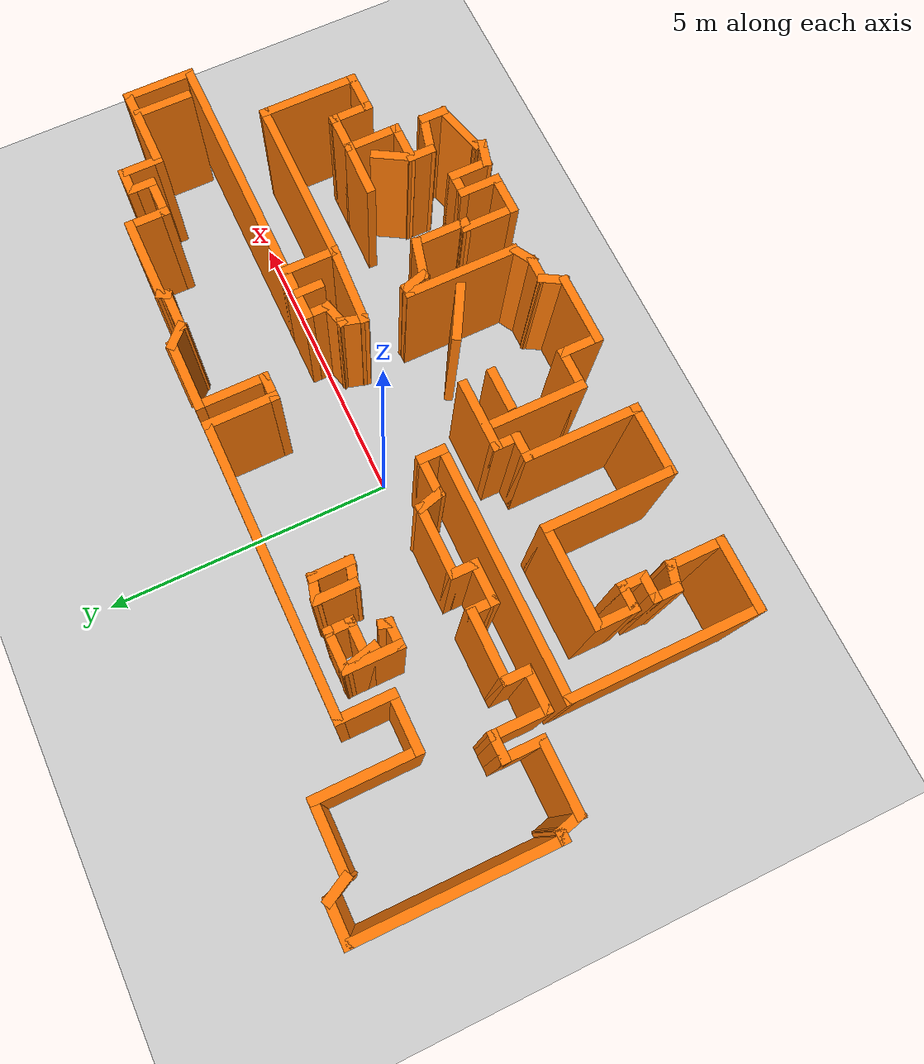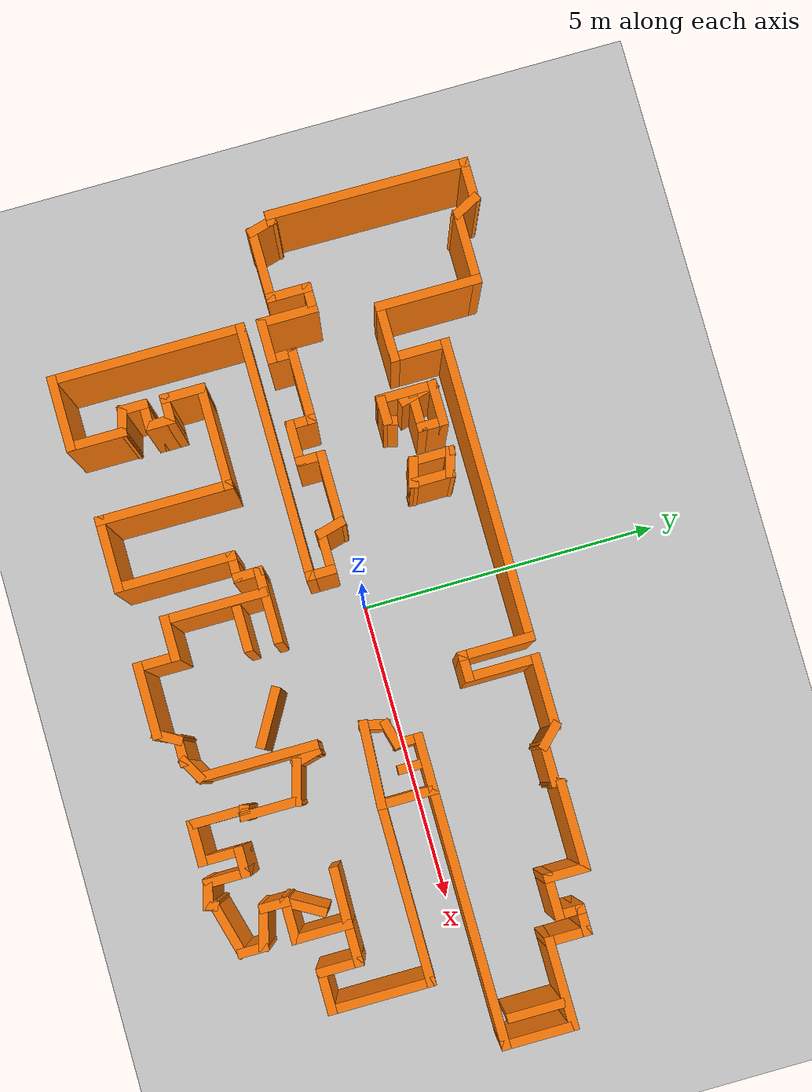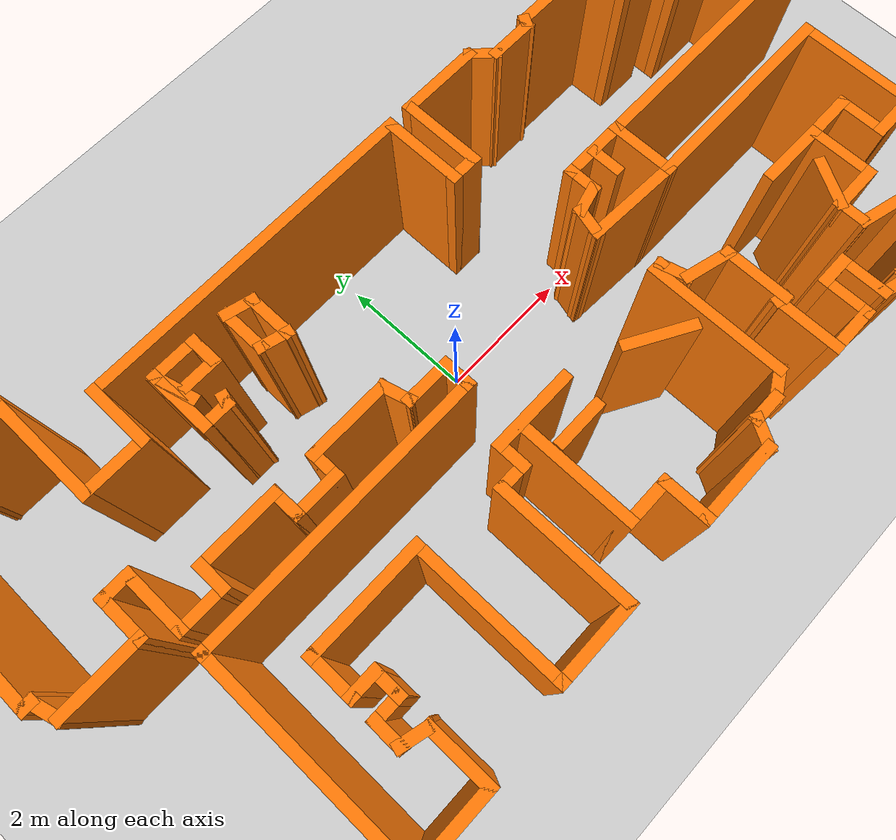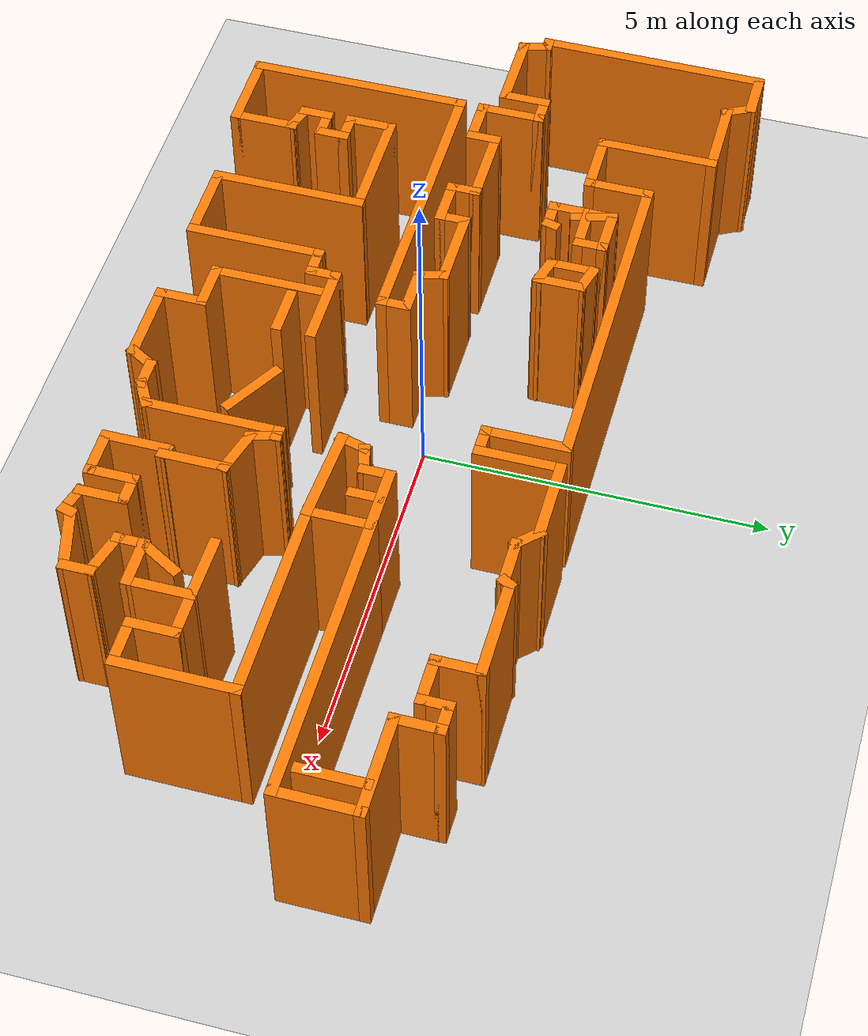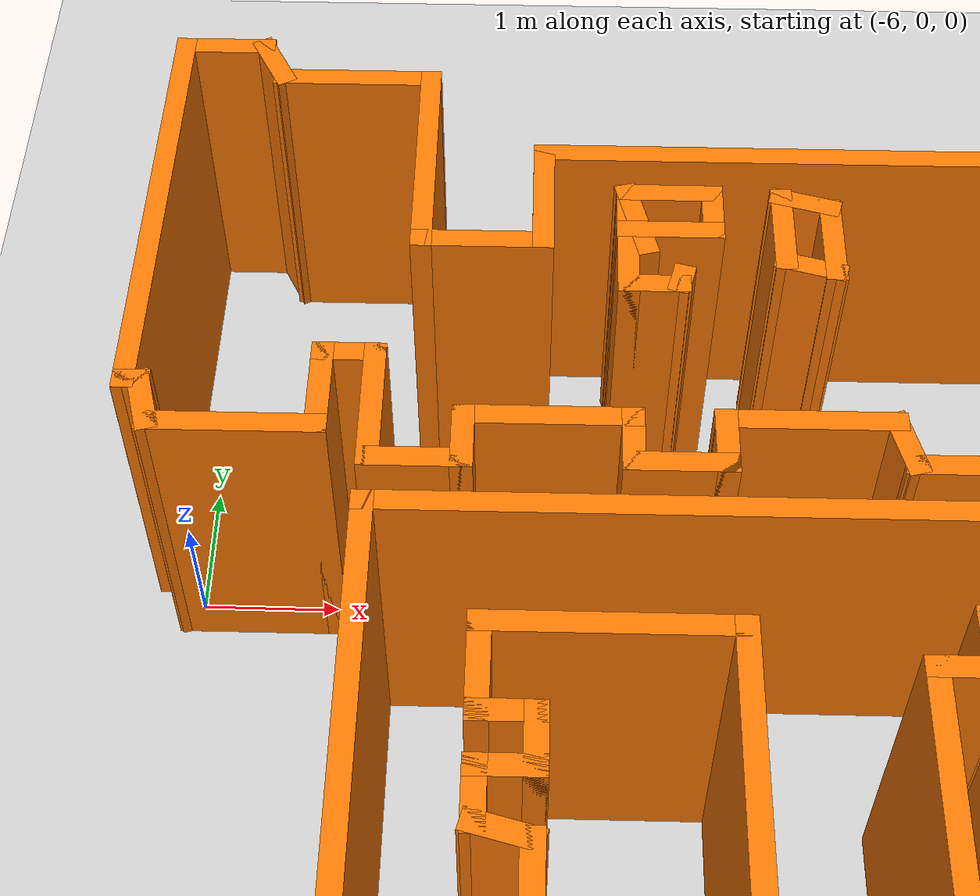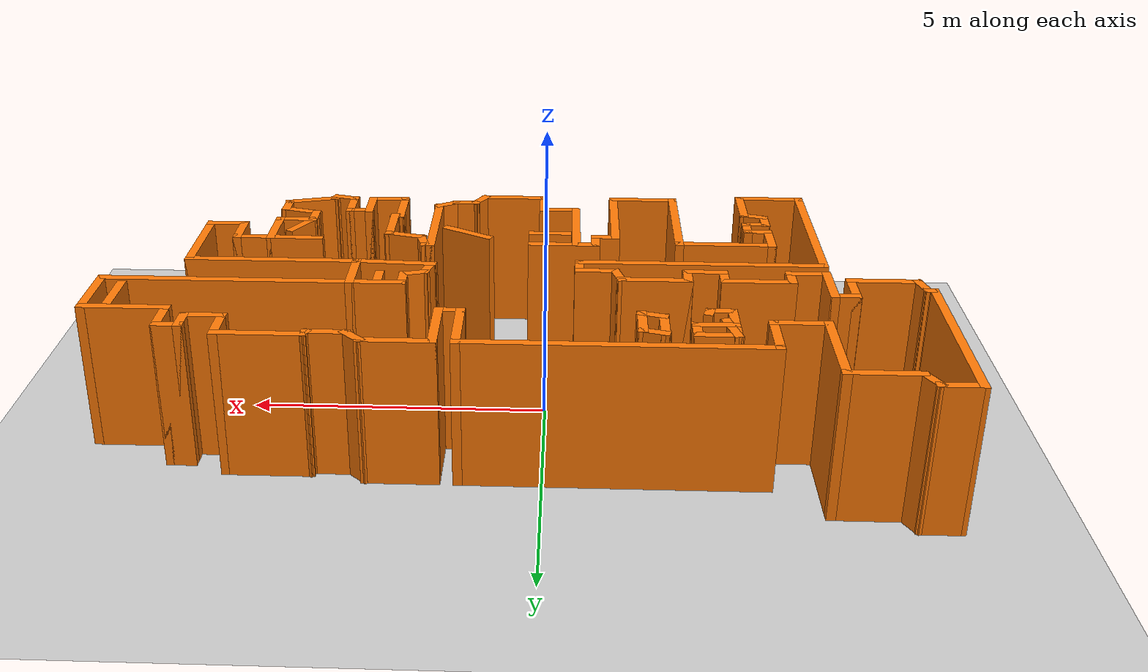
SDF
<sdf version="1.6">
 <world name="default">
  <light name="sun" type="directional">
   <pose>0 0 10 0 -0 0</pose>
   <diffuse>0.8 0.8 0.8 1</diffuse>
   <specular>0.2 0.2 0.2 1</specular>
   <attenuation>
    <range>1000</range>
    <constant>0.9</constant>
    <linear>0.01</linear>
    <quadratic>0.001</quadratic>
   </attenuation>
   <direction>-0.5 0.1 -0.9</direction>
  </light>
  <model name="ground_plane">
   <static>1</static>
   <link name="link">
    <collision name="collision">
     <geometry><plane><normal>0 0 1</normal><size>100 100</size></plane></geometry>
     <surface>
      <contact><collide_bitmask>65535</collide_bitmask></contact>
      <friction><ode><mu>100</mu><mu2>50</mu2></ode></friction>
     </surface>
    </collision>
    <visual name="visual">
     <cast_shadows>0</cast_shadows>
     <geometry><plane><normal>0 0 1</normal><size>100 100</size></plane></geometry>
     <material>
      <script><uri>file://media/materials/scripts/gazebo.material</uri><name>Gazebo/Grey</name></script>
     </material>
    </visual>
   </link>
  </model>
  <gravity>0 0 -9.8</gravity>
  <magnetic_field>6e-06 2.3e-05 -4.2e-05</magnetic_field>
  <atmosphere type="adiabatic"/>
  <physics name="default_physics" default="0" type="ode">
   <max_step_size>0.001</max_step_size>
   <real_time_factor>1</real_time_factor>
   <real_time_update_rate>1000</real_time_update_rate>
  </physics>
  <scene><ambient>0.4 0.4 0.4 1</ambient><background>0.7 0.7 0.7 1</background><shadows>1</shadows></scene>
  <audio><device>default</device></audio>
  <spherical_coordinates>
   <surface_model>EARTH_WGS84</surface_model>
   <latitude_deg>0</latitude_deg>
   <longitude_deg>0</longitude_deg>
   <elevation>0</elevation>
   <heading_deg>0</heading_deg>
  </spherical_coordinates>
  <model name="map_27">
   <pose>0.519139 -0.186386 0 0 -0 0</pose>
   <link name="Wall_100">
    <collision name="Wall_100_Collision">
     <geometry><box><size>0.75 0.15 2.5</size></box></geometry>
     <pose>0 0 1.25 0 -0 0</pose>
    </collision>
    <visual name="Wall_100_Visual">
     <pose>0 0 1.25 0 -0 0</pose>
     <geometry><box><size>0.75 0.15 2.5</size></box></geometry>
     <material>
      <script><uri>file://media/materials/scripts/gazebo.material</uri><name>Gazebo/Grey</name></script>
      <ambient>0.996078 0.47451 0.0196078 1</ambient>
     </material>
     <meta><layer>0</layer></meta>
    </visual>
    <pose>4.04514 -2.2771 0 0 -0 0</pose>
   </link>
   <link name="Wall_101">
    <collision name="Wall_101_Collision">
     <geometry><box><size>1 0.15 2.5</size></box></geometry>
     <pose>0 0 1.25 0 -0 0</pose>
    </collision>
    <visual name="Wall_101_Visual">
     <pose>0 0 1.25 0 -0 0</pose>
     <geometry><box><size>1 0.15 2.5</size></box></geometry>
     <material>
      <script><uri>file://media/materials/scripts/gazebo.material</uri><name>Gazebo/Grey</name></script>
      <ambient>0.996078 0.47451 0.0196078 1</ambient>
     </material>
     <meta><layer>0</layer></meta>
    </visual>
    <pose>4.34514 -1.8521 0 0 -0 1.5708</pose>
   </link>
   <link name="Wall_102">
    <collision name="Wall_102_Collision">
     <geometry><box><size>0.75 0.15 2.5</size></box></geometry>
     <pose>0 0 1.25 0 -0 0</pose>
    </collision>
    <visual name="Wall_102_Visual">
     <pose>0 0 1.25 0 -0 0</pose>
     <geometry><box><size>0.75 0.15 2.5</size></box></geometry>
     <material>
      <script><uri>file://media/materials/scripts/gazebo.material</uri><name>Gazebo/Grey</name></script>
      <ambient>0.996078 0.47451 0.0196078 1</ambient>
     </material>
     <meta><layer>0</layer></meta>
    </visual>
    <pose>4.64514 -1.4271 0 0 -0 0</pose>
   </link>
   <link name="Wall_103">
    <collision name="Wall_103_Collision">
     <geometry><box><size>0.75 0.15 2.5</size></box></geometry>
     <pose>0 0 1.25 0 -0 0</pose>
    </collision>
    <visual name="Wall_103_Visual">
     <pose>0 0 1.25 0 -0 0</pose>
     <geometry><box><size>0.75 0.15 2.5</size></box></geometry>
     <material>
      <script><uri>file://media/materials/scripts/gazebo.material</uri><name>Gazebo/Grey</name></script>
      <ambient>0.996078 0.47451 0.0196078 1</ambient>
     </material>
     <meta><layer>0</layer></meta>
    </visual>
    <pose>4.94514 -1.7271 0 0 -0 -1.5708</pose>
   </link>
   <link name="Wall_104">
    <collision name="Wall_104_Collision">
     <geometry><box><size>0.75 0.15 2.5</size></box></geometry>
     <pose>0 0 1.25 0 -0 0</pose>
    </collision>
    <visual name="Wall_104_Visual">
     <pose>0 0 1.25 0 -0 0</pose>
     <geometry><box><size>0.75 0.15 2.5</size></box></geometry>
     <material>
      <script><uri>file://media/materials/scripts/gazebo.material</uri><name>Gazebo/Grey</name></script>
      <ambient>0.996078 0.47451 0.0196078 1</ambient>
     </material>
     <meta><layer>0</layer></meta>
    </visual>
    <pose>5.24514 -2.0271 0 0 -0 0</pose>
   </link>
   <link name="Wall_105">
    <collision name="Wall_105_Collision">
     <geometry><box><size>1.75 0.15 2.5</size></box></geometry>
     <pose>0 0 1.25 0 -0 0</pose>
    </collision>
    <visual name="Wall_105_Visual">
     <pose>0 0 1.25 0 -0 0</pose>
     <geometry><box><size>1.75 0.15 2.5</size></box></geometry>
     <material>
      <script><uri>file://media/materials/scripts/gazebo.material</uri><name>Gazebo/Grey</name></script>
      <ambient>0.996078 0.47451 0.0196078 1</ambient>
     </material>
     <meta><layer>0</layer></meta>
    </visual>
    <pose>5.54514 -1.2271 0 0 -0 1.5708</pose>
   </link>
   <link name="Wall_106">
    <collision name="Wall_106_Collision">
     <geometry><box><size>3 0.15 2.5</size></box></geometry>
     <pose>0 0 1.25 0 -0 0</pose>
    </collision>
    <visual name="Wall_106_Visual">
     <pose>0 0 1.25 0 -0 0</pose>
     <geometry><box><size>3 0.15 2.5</size></box></geometry>
     <material>
      <script><uri>file://media/materials/scripts/gazebo.material</uri><name>Gazebo/Grey</name></script>
      <ambient>0.996078 0.47451 0.0196078 1</ambient>
     </material>
     <meta><layer>0</layer></meta>
    </visual>
    <pose>4.12014 -0.427096 0 0 -0 3.14159</pose>
   </link>
   <link name="Wall_107">
    <collision name="Wall_107_Collision">
     <geometry><box><size>1 0.15 2.5</size></box></geometry>
     <pose>0 0 1.25 0 -0 0</pose>
    </collision>
    <visual name="Wall_107_Visual">
     <pose>0 0 1.25 0 -0 0</pose>
     <geometry><box><size>1 0.15 2.5</size></box></geometry>
     <material>
      <script><uri>file://media/materials/scripts/gazebo.material</uri><name>Gazebo/Grey</name></script>
      <ambient>0.996078 0.47451 0.0196078 1</ambient>
     </material>
     <meta><layer>0</layer></meta>
    </visual>
    <pose>2.69514 -0.002096 0 0 -0 1.5708</pose>
   </link>
   <link name="Wall_108">
    <collision name="Wall_108_Collision">
     <geometry><box><size>4.25 0.15 2.5</size></box></geometry>
     <pose>0 0 1.25 0 -0 0</pose>
    </collision>
    <visual name="Wall_108_Visual">
     <pose>0 0 1.25 0 -0 0</pose>
     <geometry><box><size>4.25 0.15 2.5</size></box></geometry>
     <material>
      <script><uri>file://media/materials/scripts/gazebo.material</uri><name>Gazebo/Grey</name></script>
      <ambient>0.996078 0.47451 0.0196078 1</ambient>
     </material>
     <meta><layer>0</layer></meta>
    </visual>
    <pose>4.74514 0.422904 0 0 -0 0</pose>
   </link>
   <link name="Wall_109">
    <collision name="Wall_109_Collision">
     <geometry><box><size>1.25 0.15 2.5</size></box></geometry>
     <pose>0 0 1.25 0 -0 0</pose>
    </collision>
    <visual name="Wall_109_Visual">
     <pose>0 0 1.25 0 -0 0</pose>
     <geometry><box><size>1.25 0.15 2.5</size></box></geometry>
     <material>
      <script><uri>file://media/materials/scripts/gazebo.material</uri><name>Gazebo/Grey</name></script>
      <ambient>0.996078 0.47451 0.0196078 1</ambient>
     </material>
     <meta><layer>0</layer></meta>
    </visual>
    <pose>6.79514 0.972904 0 0 -0 1.5708</pose>
   </link>
   <link name="Wall_110">
    <collision name="Wall_110_Collision">
     <geometry><box><size>1.5 0.15 2.5</size></box></geometry>
     <pose>0 0 1.25 0 -0 0</pose>
    </collision>
    <visual name="Wall_110_Visual">
     <pose>0 0 1.25 0 -0 0</pose>
     <geometry><box><size>1.5 0.15 2.5</size></box></geometry>
     <material>
      <script><uri>file://media/materials/scripts/gazebo.material</uri><name>Gazebo/Grey</name></script>
      <ambient>0.996078 0.47451 0.0196078 1</ambient>
     </material>
     <meta><layer>0</layer></meta>
    </visual>
    <pose>6.12014 1.5229 0 0 -0 3.14159</pose>
   </link>
   <link name="Wall_111">
    <collision name="Wall_111_Collision">
     <geometry><box><size>0.75 0.15 2.5</size></box></geometry>
     <pose>0 0 1.25 0 -0 0</pose>
    </collision>
    <visual name="Wall_111_Visual">
     <pose>0 0 1.25 0 -0 0</pose>
     <geometry><box><size>0.75 0.15 2.5</size></box></geometry>
     <material>
      <script><uri>file://media/materials/scripts/gazebo.material</uri><name>Gazebo/Grey</name></script>
      <ambient>0.996078 0.47451 0.0196078 1</ambient>
     </material>
     <meta><layer>0</layer></meta>
    </visual>
    <pose>5.44514 1.8229 0 0 -0 1.5708</pose>
   </link>
   <link name="Wall_112">
    <collision name="Wall_112_Collision">
     <geometry><box><size>0.5 0.15 2.5</size></box></geometry>
     <pose>0 0 1.25 0 -0 0</pose>
    </collision>
    <visual name="Wall_112_Visual">
     <pose>0 0 1.25 0 -0 0</pose>
     <geometry><box><size>0.5 0.15 2.5</size></box></geometry>
     <material>
      <script><uri>file://media/materials/scripts/gazebo.material</uri><name>Gazebo/Grey</name></script>
      <ambient>0.996078 0.47451 0.0196078 1</ambient>
     </material>
     <meta><layer>0</layer></meta>
    </visual>
    <pose>5.27014 2.1229 0 0 -0 3.14159</pose>
   </link>
   <link name="Wall_113">
    <collision name="Wall_113_Collision">
     <geometry><box><size>0.5 0.15 2.5</size></box></geometry>
     <pose>0 0 1.25 0 -0 0</pose>
    </collision>
    <visual name="Wall_113_Visual">
     <pose>0 0 1.25 0 -0 0</pose>
     <geometry><box><size>0.5 0.15 2.5</size></box></geometry>
     <material>
      <script><uri>file://media/materials/scripts/gazebo.material</uri><name>Gazebo/Grey</name></script>
      <ambient>0.996078 0.47451 0.0196078 1</ambient>
     </material>
     <meta><layer>0</layer></meta>
    </visual>
    <pose>5.09514 1.9479 0 0 -0 -1.5708</pose>
   </link>
   <link name="Wall_114">
    <collision name="Wall_114_Collision">
     <geometry><box><size>0.75 0.15 2.5</size></box></geometry>
     <pose>0 0 1.25 0 -0 0</pose>
    </collision>
    <visual name="Wall_114_Visual">
     <pose>0 0 1.25 0 -0 0</pose>
     <geometry><box><size>0.75 0.15 2.5</size></box></geometry>
     <material>
      <script><uri>file://media/materials/scripts/gazebo.material</uri><name>Gazebo/Grey</name></script>
      <ambient>0.996078 0.47451 0.0196078 1</ambient>
     </material>
     <meta><layer>0</layer></meta>
    </visual>
    <pose>4.79514 1.7729 0 0 -0 3.14159</pose>
   </link>
   <link name="Wall_115">
    <collision name="Wall_115_Collision">
     <geometry><box><size>0.75 0.15 2.5</size></box></geometry>
     <pose>0 0 1.25 0 -0 0</pose>
    </collision>
    <visual name="Wall_115_Visual">
     <pose>0 0 1.25 0 -0 0</pose>
     <geometry><box><size>0.75 0.15 2.5</size></box></geometry>
     <material>
      <script><uri>file://media/materials/scripts/gazebo.material</uri><name>Gazebo/Grey</name></script>
      <ambient>0.996078 0.47451 0.0196078 1</ambient>
     </material>
     <meta><layer>0</layer></meta>
    </visual>
    <pose>4.49514 2.0729 0 0 -0 1.5708</pose>
   </link>
   <link name="Wall_116">
    <collision name="Wall_116_Collision">
     <geometry><box><size>1.5 0.15 2.5</size></box></geometry>
     <pose>0 0 1.25 0 -0 0</pose>
    </collision>
    <visual name="Wall_116_Visual">
     <pose>0 0 1.25 0 -0 0</pose>
     <geometry><box><size>1.5 0.15 2.5</size></box></geometry>
     <material>
      <script><uri>file://media/materials/scripts/gazebo.material</uri><name>Gazebo/Grey</name></script>
      <ambient>0.996078 0.47451 0.0196078 1</ambient>
     </material>
     <meta><layer>0</layer></meta>
    </visual>
    <pose>3.82014 2.3729 0 0 -0 3.14159</pose>
   </link>
   <link name="Wall_117">
    <collision name="Wall_117_Collision">
     <geometry><box><size>0.25 0.15 2.5</size></box></geometry>
     <pose>0 0 1.25 0 -0 0</pose>
    </collision>
    <visual name="Wall_117_Visual">
     <pose>0 0 1.25 0 -0 0</pose>
     <geometry><box><size>0.25 0.15 2.5</size></box></geometry>
     <material>
      <script><uri>file://media/materials/scripts/gazebo.material</uri><name>Gazebo/Grey</name></script>
      <ambient>0.996078 0.47451 0.0196078 1</ambient>
     </material>
     <meta><layer>0</layer></meta>
    </visual>
    <pose>3.12014 2.3296 0 0 -0 -2.0944</pose>
   </link>
   <link name="Wall_118">
    <collision name="Wall_118_Collision">
     <geometry><box><size>0.75 0.15 2.5</size></box></geometry>
     <pose>0 0 1.25 0 -0 0</pose>
    </collision>
    <visual name="Wall_118_Visual">
     <pose>0 0 1.25 0 -0 0</pose>
     <geometry><box><size>0.75 0.15 2.5</size></box></geometry>
     <material>
      <script><uri>file://media/materials/scripts/gazebo.material</uri><name>Gazebo/Grey</name></script>
      <ambient>0.996078 0.47451 0.0196078 1</ambient>
     </material>
     <meta><layer>0</layer></meta>
    </visual>
    <pose>2.79514 2.2863 0 0 -0 3.14159</pose>
   </link>
   <link name="Wall_119">
    <collision name="Wall_119_Collision">
     <geometry><box><size>0.5 0.15 2.5</size></box></geometry>
     <pose>0 0 1.25 0 -0 0</pose>
    </collision>
    <visual name="Wall_119_Visual">
     <pose>0 0 1.25 0 -0 0</pose>
     <geometry><box><size>0.5 0.15 2.5</size></box></geometry>
     <material>
      <script><uri>file://media/materials/scripts/gazebo.material</uri><name>Gazebo/Grey</name></script>
      <ambient>0.996078 0.47451 0.0196078 1</ambient>
     </material>
     <meta><layer>0</layer></meta>
    </visual>
    <pose>2.3714 2.41005 0 0 -0 2.35619</pose>
   </link>
   <link name="Wall_120">
    <collision name="Wall_120_Collision">
     <geometry><box><size>1.25 0.15 2.5</size></box></geometry>
     <pose>0 0 1.25 0 -0 0</pose>
    </collision>
    <visual name="Wall_120_Visual">
     <pose>0 0 1.25 0 -0 0</pose>
     <geometry><box><size>1.25 0.15 2.5</size></box></geometry>
     <material>
      <script><uri>file://media/materials/scripts/gazebo.material</uri><name>Gazebo/Grey</name></script>
      <ambient>0.996078 0.47451 0.0196078 1</ambient>
     </material>
     <meta><layer>0</layer></meta>
    </visual>
    <pose>1.69765 2.53379 0 0 -0 3.14159</pose>
   </link>
   <link name="Wall_121">
    <collision name="Wall_121_Collision">
     <geometry><box><size>1.25 0.15 2.5</size></box></geometry>
     <pose>0 0 1.25 0 -0 0</pose>
    </collision>
    <visual name="Wall_121_Visual">
     <pose>0 0 1.25 0 -0 0</pose>
     <geometry><box><size>1.25 0.15 2.5</size></box></geometry>
     <material>
      <script><uri>file://media/materials/scripts/gazebo.material</uri><name>Gazebo/Grey</name></script>
      <ambient>0.996078 0.47451 0.0196078 1</ambient>
     </material>
     <meta><layer>0</layer></meta>
    </visual>
    <pose>1.14766 1.98379 0 0 -0 -1.5708</pose>
   </link>
   <link name="Wall_122">
    <collision name="Wall_122_Collision">
     <geometry><box><size>0.5 0.15 2.5</size></box></geometry>
     <pose>0 0 1.25 0 -0 0</pose>
    </collision>
    <visual name="Wall_122_Visual">
     <pose>0 0 1.25 0 -0 0</pose>
     <geometry><box><size>0.5 0.15 2.5</size></box></geometry>
     <material>
      <script><uri>file://media/materials/scripts/gazebo.material</uri><name>Gazebo/Grey</name></script>
      <ambient>0.996078 0.47451 0.0196078 1</ambient>
     </material>
     <meta><layer>0</layer></meta>
    </visual>
    <pose>0.972655 1.43379 0 0 -0 3.14159</pose>
   </link>
   <link name="Wall_123">
    <collision name="Wall_123_Collision">
     <geometry><box><size>1.25 0.15 2.5</size></box></geometry>
     <pose>0 0 1.25 0 -0 0</pose>
    </collision>
    <visual name="Wall_123_Visual">
     <pose>0 0 1.25 0 -0 0</pose>
     <geometry><box><size>1.25 0.15 2.5</size></box></geometry>
     <material>
      <script><uri>file://media/materials/scripts/gazebo.material</uri><name>Gazebo/Grey</name></script>
      <ambient>0.996078 0.47451 0.0196078 1</ambient>
     </material>
     <meta><layer>0</layer></meta>
    </visual>
    <pose>0.797655 1.98379 0 0 -0 1.5708</pose>
   </link>
   <link name="Wall_124">
    <collision name="Wall_124_Collision">
     <geometry><box><size>5 0.15 2.5</size></box></geometry>
     <pose>0 0 1.25 0 -0 0</pose>
    </collision>
    <visual name="Wall_124_Visual">
     <pose>0 0 1.25 0 -0 0</pose>
     <geometry><box><size>5 0.15 2.5</size></box></geometry>
     <material>
      <script><uri>file://media/materials/scripts/gazebo.material</uri><name>Gazebo/Grey</name></script>
      <ambient>0.996078 0.47451 0.0196078 1</ambient>
     </material>
     <meta><layer>0</layer></meta>
    </visual>
    <pose>-1.62735 2.53379 0 0 -0 3.14159</pose>
   </link>
   <link name="Wall_125">
    <collision name="Wall_125_Collision">
     <geometry><box><size>1 0.15 2.5</size></box></geometry>
     <pose>0 0 1.25 0 -0 0</pose>
    </collision>
    <visual name="Wall_125_Visual">
     <pose>0 0 1.25 0 -0 0</pose>
     <geometry><box><size>1 0.15 2.5</size></box></geometry>
     <material>
      <script><uri>file://media/materials/scripts/gazebo.material</uri><name>Gazebo/Grey</name></script>
      <ambient>0.996078 0.47451 0.0196078 1</ambient>
     </material>
     <meta><layer>0</layer></meta>
    </visual>
    <pose>-4.05234 2.10879 0 0 -0 -1.5708</pose>
   </link>
   <link name="Wall_126">
    <collision name="Wall_126_Collision">
     <geometry><box><size>1 0.15 2.5</size></box></geometry>
     <pose>0 0 1.25 0 -0 0</pose>
    </collision>
    <visual name="Wall_126_Visual">
     <pose>0 0 1.25 0 -0 0</pose>
     <geometry><box><size>1 0.15 2.5</size></box></geometry>
     <material>
      <script><uri>file://media/materials/scripts/gazebo.material</uri><name>Gazebo/Grey</name></script>
      <ambient>0.996078 0.47451 0.0196078 1</ambient>
     </material>
     <meta><layer>0</layer></meta>
    </visual>
    <pose>-4.47734 1.68379 0 0 -0 3.14159</pose>
   </link>
   <link name="Wall_127">
    <collision name="Wall_127_Collision">
     <geometry><box><size>1.75 0.15 2.5</size></box></geometry>
     <pose>0 0 1.25 0 -0 0</pose>
    </collision>
    <visual name="Wall_127_Visual">
     <pose>0 0 1.25 0 -0 0</pose>
     <geometry><box><size>1.75 0.15 2.5</size></box></geometry>
     <material>
      <script><uri>file://media/materials/scripts/gazebo.material</uri><name>Gazebo/Grey</name></script>
      <ambient>0.996078 0.47451 0.0196078 1</ambient>
     </material>
     <meta><layer>0</layer></meta>
    </visual>
    <pose>-4.90235 2.48379 0 0 -0 1.5708</pose>
   </link>
   <link name="Wall_128">
    <collision name="Wall_128_Collision">
     <geometry><box><size>1.25 0.15 2.5</size></box></geometry>
     <pose>0 0 1.25 0 -0 0</pose>
    </collision>
    <visual name="Wall_128_Visual">
     <pose>0 0 1.25 0 -0 0</pose>
     <geometry><box><size>1.25 0.15 2.5</size></box></geometry>
     <material>
      <script><uri>file://media/materials/scripts/gazebo.material</uri><name>Gazebo/Grey</name></script>
      <ambient>0.996078 0.47451 0.0196078 1</ambient>
     </material>
     <meta><layer>0</layer></meta>
    </visual>
    <pose>-5.45235 3.28379 0 0 -0 3.14159</pose>
   </link>
   <link name="Wall_132">
    <collision name="Wall_132_Collision">
     <geometry><box><size>0.75 0.15 2.5</size></box></geometry>
     <pose>0 0 1.25 0 -0 0</pose>
    </collision>
    <visual name="Wall_132_Visual">
     <pose>0 0 1.25 0 -0 0</pose>
     <geometry><box><size>0.75 0.15 2.5</size></box></geometry>
     <material>
      <script><uri>file://media/materials/scripts/gazebo.material</uri><name>Gazebo/Grey</name></script>
      <ambient>0.996078 0.47451 0.0196078 1</ambient>
     </material>
     <meta><layer>0</layer></meta>
    </visual>
    <pose>-6.47147 3.6078 0 0 -0 0</pose>
   </link>
   <link name="Wall_133">
    <collision name="Wall_133_Collision">
     <geometry><box><size>0.515501 0.15 2.5</size></box></geometry>
     <pose>0 0 1.25 0 -0 0</pose>
    </collision>
    <visual name="Wall_133_Visual">
     <pose>0 0 1.25 0 -0 0</pose>
     <geometry><box><size>0.515501 0.15 2.5</size></box></geometry>
     <material>
      <script><uri>file://media/materials/scripts/gazebo.material</uri><name>Gazebo/Grey</name></script>
      <ambient>0.996078 0.47451 0.0196078 1</ambient>
     </material>
     <meta><layer>0</layer></meta>
    </visual>
    <pose>-6.08691 3.4458 0 0 -0 -1.08972</pose>
   </link>
   <link name="Wall_135">
    <collision name="Wall_135_Collision">
     <geometry><box><size>1 0.15 2.5</size></box></geometry>
     <pose>0 0 1.25 0 -0 0</pose>
    </collision>
    <visual name="Wall_135_Visual">
     <pose>0 0 1.25 0 -0 0</pose>
     <geometry><box><size>1 0.15 2.5</size></box></geometry>
     <material>
      <script><uri>file://media/materials/scripts/gazebo.material</uri><name>Gazebo/Grey</name></script>
      <ambient>0.996078 0.47451 0.0196078 1</ambient>
     </material>
     <meta><layer>0</layer></meta>
    </visual>
    <pose>6.41297 1.05479 0 0 -0 -1.5708</pose>
   </link>
   <link name="Wall_138">
    <collision name="Wall_138_Collision">
     <geometry><box><size>1 0.15 2.5</size></box></geometry>
     <pose>0 0 1.25 0 -0 0</pose>
    </collision>
    <visual name="Wall_138_Visual">
     <pose>0 0 1.25 0 -0 0</pose>
     <geometry><box><size>1 0.15 2.5</size></box></geometry>
     <material>
      <script><uri>file://media/materials/scripts/gazebo.material</uri><name>Gazebo/Grey</name></script>
      <ambient>0.996078 0.47451 0.0196078 1</ambient>
     </material>
     <meta><layer>0</layer></meta>
    </visual>
    <pose>0.905858 -1.76282 0 0 -0 -0.523599</pose>
   </link>
   <link name="Wall_141">
    <collision name="Wall_141_Collision">
     <geometry><box><size>0.99677 0.15 2.5</size></box></geometry>
     <pose>0 0 1.25 0 -0 0</pose>
    </collision>
    <visual name="Wall_141_Visual">
     <pose>0 0 1.25 0 -0 0</pose>
     <geometry><box><size>0.99677 0.15 2.5</size></box></geometry>
     <material>
      <script><uri>file://media/materials/scripts/gazebo.material</uri><name>Gazebo/Grey</name></script>
      <ambient>0.996078 0.47451 0.0196078 1</ambient>
     </material>
     <meta><layer>0</layer></meta>
    </visual>
    <pose>3.92183 -1.41932 0 0 -0 -0.018375</pose>
   </link>
   <link name="Wall_143">
    <collision name="Wall_143_Collision">
     <geometry><box><size>0.75 0.15 2.5</size></box></geometry>
     <pose>0 0 1.25 0 -0 0</pose>
    </collision>
    <visual name="Wall_143_Visual">
     <pose>0 0 1.25 0 -0 0</pose>
     <geometry><box><size>0.75 0.15 2.5</size></box></geometry>
     <material>
      <script><uri>file://media/materials/scripts/gazebo.material</uri><name>Gazebo/Grey</name></script>
      <ambient>0.996078 0.47451 0.0196078 1</ambient>
     </material>
     <meta><layer>0</layer></meta>
    </visual>
    <pose>3.89514 -2.01729 0 0 -0 1.0472</pose>
   </link>
   <link name="Wall_148">
    <collision name="Wall_148_Collision">
     <geometry><box><size>1 0.15 2.5</size></box></geometry>
     <pose>0 0 1.25 0 -0 0</pose>
    </collision>
    <visual name="Wall_148_Visual">
     <pose>0 0 1.25 0 -0 0</pose>
     <geometry><box><size>1 0.15 2.5</size></box></geometry>
     <material>
      <script><uri>file://media/materials/scripts/gazebo.material</uri><name>Gazebo/Grey</name></script>
      <ambient>0.996078 0.47451 0.0196078 1</ambient>
     </material>
     <meta><layer>0</layer></meta>
    </visual>
    <pose>-3.4638 1.72558 0 0 -0 -1.5708</pose>
   </link>
   <link name="Wall_149">
    <collision name="Wall_149_Collision">
     <geometry><box><size>0.5 0.15 2.5</size></box></geometry>
     <pose>0 0 1.25 0 -0 0</pose>
    </collision>
    <visual name="Wall_149_Visual">
     <pose>0 0 1.25 0 -0 0</pose>
     <geometry><box><size>0.5 0.15 2.5</size></box></geometry>
     <material>
      <script><uri>file://media/materials/scripts/gazebo.material</uri><name>Gazebo/Grey</name></script>
      <ambient>0.996078 0.47451 0.0196078 1</ambient>
     </material>
     <meta><layer>0</layer></meta>
    </visual>
    <pose>-3.2888 1.30058 0 0 -0 0</pose>
   </link>
   <link name="Wall_15">
    <collision name="Wall_15_Collision">
     <geometry><box><size>3.36574 0.15 2.5</size></box></geometry>
     <pose>0 0 1.25 0 -0 0</pose>
    </collision>
    <visual name="Wall_15_Visual">
     <pose>0 0 1.25 0 -0 0</pose>
     <geometry><box><size>3.36574 0.15 2.5</size></box></geometry>
     <material>
      <script><uri>file://media/materials/scripts/gazebo.material</uri><name>Gazebo/Grey</name></script>
      <ambient>0.996078 0.47451 0.0196078 1</ambient>
     </material>
     <meta><layer>0</layer></meta>
    </visual>
    <pose>-6.78304 1.99998 0 0 -0 -1.57799</pose>
   </link>
   <link name="Wall_150">
    <collision name="Wall_150_Collision">
     <geometry><box><size>0.25 0.15 2.5</size></box></geometry>
     <pose>0 0 1.25 0 -0 0</pose>
    </collision>
    <visual name="Wall_150_Visual">
     <pose>0 0 1.25 0 -0 0</pose>
     <geometry><box><size>0.25 0.15 2.5</size></box></geometry>
     <material>
      <script><uri>file://media/materials/scripts/gazebo.material</uri><name>Gazebo/Grey</name></script>
      <ambient>0.996078 0.47451 0.0196078 1</ambient>
     </material>
     <meta><layer>0</layer></meta>
    </visual>
    <pose>-3.10086 1.34887 0 0 -0 1.309</pose>
   </link>
   <link name="Wall_152">
    <collision name="Wall_152_Collision">
     <geometry><box><size>0.671958 0.15 2.5</size></box></geometry>
     <pose>0 0 1.25 0 -0 0</pose>
    </collision>
    <visual name="Wall_152_Visual">
     <pose>0 0 1.25 0 -0 0</pose>
     <geometry><box><size>0.671958 0.15 2.5</size></box></geometry>
     <material>
      <script><uri>file://media/materials/scripts/gazebo.material</uri><name>Gazebo/Grey</name></script>
      <ambient>0.996078 0.47451 0.0196078 1</ambient>
     </material>
     <meta><layer>0</layer></meta>
    </visual>
    <pose>-3.3996 1.89762 0 0 -0 1.81933</pose>
   </link>
   <link name="Wall_154">
    <collision name="Wall_154_Collision">
     <geometry><box><size>0.75 0.15 2.5</size></box></geometry>
     <pose>0 0 1.25 0 -0 0</pose>
    </collision>
    <visual name="Wall_154_Visual">
     <pose>0 0 1.25 0 -0 0</pose>
     <geometry><box><size>0.75 0.15 2.5</size></box></geometry>
     <material>
      <script><uri>file://media/materials/scripts/gazebo.material</uri><name>Gazebo/Grey</name></script>
      <ambient>0.996078 0.47451 0.0196078 1</ambient>
     </material>
     <meta><layer>0</layer></meta>
    </visual>
    <pose>-3.1638 2.15058 0 0 -0 0</pose>
   </link>
   <link name="Wall_155">
    <collision name="Wall_155_Collision">
     <geometry><box><size>0.5 0.15 2.5</size></box></geometry>
     <pose>0 0 1.25 0 -0 0</pose>
    </collision>
    <visual name="Wall_155_Visual">
     <pose>0 0 1.25 0 -0 0</pose>
     <geometry><box><size>0.5 0.15 2.5</size></box></geometry>
     <material>
      <script><uri>file://media/materials/scripts/gazebo.material</uri><name>Gazebo/Grey</name></script>
      <ambient>0.996078 0.47451 0.0196078 1</ambient>
     </material>
     <meta><layer>0</layer></meta>
    </visual>
    <pose>-2.8638 1.97558 0 0 -0 -1.5708</pose>
   </link>
   <link name="Wall_156">
    <collision name="Wall_156_Collision">
     <geometry><box><size>0.75 0.15 2.5</size></box></geometry>
     <pose>0 0 1.25 0 -0 0</pose>
    </collision>
    <visual name="Wall_156_Visual">
     <pose>0 0 1.25 0 -0 0</pose>
     <geometry><box><size>0.75 0.15 2.5</size></box></geometry>
     <material>
      <script><uri>file://media/materials/scripts/gazebo.material</uri><name>Gazebo/Grey</name></script>
      <ambient>0.996078 0.47451 0.0196078 1</ambient>
     </material>
     <meta><layer>0</layer></meta>
    </visual>
    <pose>-3.1638 1.80058 0 0 -0 3.14159</pose>
   </link>
   <link name="Wall_158">
    <collision name="Wall_158_Collision">
     <geometry><box><size>0.75 0.15 2.5</size></box></geometry>
     <pose>0 0 1.25 0 -0 0</pose>
    </collision>
    <visual name="Wall_158_Visual">
     <pose>0 0 1.25 0 -0 0</pose>
     <geometry><box><size>0.75 0.15 2.5</size></box></geometry>
     <material>
      <script><uri>file://media/materials/scripts/gazebo.material</uri><name>Gazebo/Grey</name></script>
      <ambient>0.996078 0.47451 0.0196078 1</ambient>
     </material>
     <meta><layer>0</layer></meta>
    </visual>
    <pose>-2.37666 1.82745 0 0 -0 -1.5708</pose>
   </link>
   <link name="Wall_159">
    <collision name="Wall_159_Collision">
     <geometry><box><size>0.5 0.15 2.5</size></box></geometry>
     <pose>0 0 1.25 0 -0 0</pose>
    </collision>
    <visual name="Wall_159_Visual">
     <pose>0 0 1.25 0 -0 0</pose>
     <geometry><box><size>0.5 0.15 2.5</size></box></geometry>
     <material>
      <script><uri>file://media/materials/scripts/gazebo.material</uri><name>Gazebo/Grey</name></script>
      <ambient>0.996078 0.47451 0.0196078 1</ambient>
     </material>
     <meta><layer>0</layer></meta>
    </visual>
    <pose>-2.20762 1.48215 0 0 -0 -0.261799</pose>
   </link>
   <link name="Wall_16">
    <collision name="Wall_16_Collision">
     <geometry><box><size>0.25 0.15 2.5</size></box></geometry>
     <pose>0 0 1.25 0 -0 0</pose>
    </collision>
    <visual name="Wall_16_Visual">
     <pose>0 0 1.25 0 -0 0</pose>
     <geometry><box><size>0.25 0.15 2.5</size></box></geometry>
     <material>
      <script><uri>file://media/materials/scripts/gazebo.material</uri><name>Gazebo/Grey</name></script>
      <ambient>0.996078 0.47451 0.0196078 1</ambient>
     </material>
     <meta><layer>0</layer></meta>
    </visual>
    <pose>-6.7446 0.392152 0 0 -0 0</pose>
   </link>
   <link name="Wall_160">
    <collision name="Wall_160_Collision">
     <geometry><box><size>0.75 0.15 2.5</size></box></geometry>
     <pose>0 0 1.25 0 -0 0</pose>
    </collision>
    <visual name="Wall_160_Visual">
     <pose>0 0 1.25 0 -0 0</pose>
     <geometry><box><size>0.75 0.15 2.5</size></box></geometry>
     <material>
      <script><uri>file://media/materials/scripts/gazebo.material</uri><name>Gazebo/Grey</name></script>
      <ambient>0.996078 0.47451 0.0196078 1</ambient>
     </material>
     <meta><layer>0</layer></meta>
    </visual>
    <pose>-2.03858 1.73686 0 0 -0 1.5708</pose>
   </link>
   <link name="Wall_161">
    <collision name="Wall_161_Collision">
     <geometry><box><size>0.5 0.15 2.5</size></box></geometry>
     <pose>0 0 1.25 0 -0 0</pose>
    </collision>
    <visual name="Wall_161_Visual">
     <pose>0 0 1.25 0 -0 0</pose>
     <geometry><box><size>0.5 0.15 2.5</size></box></geometry>
     <material>
      <script><uri>file://media/materials/scripts/gazebo.material</uri><name>Gazebo/Grey</name></script>
      <ambient>0.996078 0.47451 0.0196078 1</ambient>
     </material>
     <meta><layer>0</layer></meta>
    </visual>
    <pose>-2.20762 2.08215 0 0 -0 2.87979</pose>
   </link>
   <link name="Wall_164">
    <collision name="Wall_164_Collision">
     <geometry><box><size>0.75 0.15 2.5</size></box></geometry>
     <pose>0 0 1.25 0 -0 0</pose>
    </collision>
    <visual name="Wall_164_Visual">
     <pose>0 0 1.25 0 -0 0</pose>
     <geometry><box><size>0.75 0.15 2.5</size></box></geometry>
     <material>
      <script><uri>file://media/materials/scripts/gazebo.material</uri><name>Gazebo/Grey</name></script>
      <ambient>0.996078 0.47451 0.0196078 1</ambient>
     </material>
     <meta><layer>0</layer></meta>
    </visual>
    <pose>-0.550039 -1.78163 0 0 -0 0</pose>
   </link>
   <link name="Wall_167">
    <collision name="Wall_167_Collision">
     <geometry><box><size>1 0.15 2.5</size></box></geometry>
     <pose>0 0 1.25 0 -0 0</pose>
    </collision>
    <visual name="Wall_167_Visual">
     <pose>0 0 1.25 0 -0 0</pose>
     <geometry><box><size>1 0.15 2.5</size></box></geometry>
     <material>
      <script><uri>file://media/materials/scripts/gazebo.material</uri><name>Gazebo/Grey</name></script>
      <ambient>0.996078 0.47451 0.0196078 1</ambient>
     </material>
     <meta><layer>0</layer></meta>
    </visual>
    <pose>2.27014 0.422904 0 0 -0 3.14159</pose>
   </link>
   <link name="Wall_168">
    <collision name="Wall_168_Collision">
     <geometry><box><size>0.5 0.15 2.5</size></box></geometry>
     <pose>0 0 1.25 0 -0 0</pose>
    </collision>
    <visual name="Wall_168_Visual">
     <pose>0 0 1.25 0 -0 0</pose>
     <geometry><box><size>0.5 0.15 2.5</size></box></geometry>
     <material>
      <script><uri>file://media/materials/scripts/gazebo.material</uri><name>Gazebo/Grey</name></script>
      <ambient>0.996078 0.47451 0.0196078 1</ambient>
     </material>
     <meta><layer>0</layer></meta>
    </visual>
    <pose>1.84514 0.247904 0 0 -0 -1.5708</pose>
   </link>
   <link name="Wall_169">
    <collision name="Wall_169_Collision">
     <geometry><box><size>0.5 0.15 2.5</size></box></geometry>
     <pose>0 0 1.25 0 -0 0</pose>
    </collision>
    <visual name="Wall_169_Visual">
     <pose>0 0 1.25 0 -0 0</pose>
     <geometry><box><size>0.5 0.15 2.5</size></box></geometry>
     <material>
      <script><uri>file://media/materials/scripts/gazebo.material</uri><name>Gazebo/Grey</name></script>
      <ambient>0.996078 0.47451 0.0196078 1</ambient>
     </material>
     <meta><layer>0</layer></meta>
    </visual>
    <pose>1.6761 0.027611 0 0 -0 -2.87979</pose>
   </link>
   <link name="Wall_17">
    <collision name="Wall_17_Collision">
     <geometry><box><size>0.5 0.15 2.5</size></box></geometry>
     <pose>0 0 1.25 0 -0 0</pose>
    </collision>
    <visual name="Wall_17_Visual">
     <pose>0 0 1.25 0 -0 0</pose>
     <geometry><box><size>0.5 0.15 2.5</size></box></geometry>
     <material>
      <script><uri>file://media/materials/scripts/gazebo.material</uri><name>Gazebo/Grey</name></script>
      <ambient>0.996078 0.47451 0.0196078 1</ambient>
     </material>
     <meta><layer>0</layer></meta>
    </visual>
    <pose>-6.64931 0.223115 0 0 -0 -1.309</pose>
   </link>
   <link name="Wall_170">
    <collision name="Wall_170_Collision">
     <geometry><box><size>0.5 0.15 2.5</size></box></geometry>
     <pose>0 0 1.25 0 -0 0</pose>
    </collision>
    <visual name="Wall_170_Visual">
     <pose>0 0 1.25 0 -0 0</pose>
     <geometry><box><size>0.5 0.15 2.5</size></box></geometry>
     <material>
      <script><uri>file://media/materials/scripts/gazebo.material</uri><name>Gazebo/Grey</name></script>
      <ambient>0.996078 0.47451 0.0196078 1</ambient>
     </material>
     <meta><layer>0</layer></meta>
    </visual>
    <pose>1.46178 -0.18672 0 0 -0 -1.8326</pose>
   </link>
   <link name="Wall_171">
    <collision name="Wall_171_Collision">
     <geometry><box><size>1.43065 0.15 2.5</size></box></geometry>
     <pose>0 0 1.25 0 -0 0</pose>
    </collision>
    <visual name="Wall_171_Visual">
     <pose>0 0 1.25 0 -0 0</pose>
     <geometry><box><size>1.43065 0.15 2.5</size></box></geometry>
     <material>
      <script><uri>file://media/materials/scripts/gazebo.material</uri><name>Gazebo/Grey</name></script>
      <ambient>0.996078 0.47451 0.0196078 1</ambient>
     </material>
     <meta><layer>0</layer></meta>
    </visual>
    <pose>2.05581 -0.391426 0 0 -0 -0.055734</pose>
   </link>
   <link name="Wall_175">
    <collision name="Wall_175_Collision">
     <geometry><box><size>0.5 0.15 2.5</size></box></geometry>
     <pose>0 0 1.25 0 -0 0</pose>
    </collision>
    <visual name="Wall_175_Visual">
     <pose>0 0 1.25 0 -0 0</pose>
     <geometry><box><size>0.5 0.15 2.5</size></box></geometry>
     <material>
      <script><uri>file://media/materials/scripts/gazebo.material</uri><name>Gazebo/Grey</name></script>
      <ambient>0.996078 0.47451 0.0196078 1</ambient>
     </material>
     <meta><layer>0</layer></meta>
    </visual>
    <pose>2.24946 0.21765 0 0 -0 -1.5708</pose>
   </link>
   <link name="Wall_18">
    <collision name="Wall_18_Collision">
     <geometry><box><size>1.25 0.15 2.5</size></box></geometry>
     <pose>0 0 1.25 0 -0 0</pose>
    </collision>
    <visual name="Wall_18_Visual">
     <pose>0 0 1.25 0 -0 0</pose>
     <geometry><box><size>1.25 0.15 2.5</size></box></geometry>
     <material>
      <script><uri>file://media/materials/scripts/gazebo.material</uri><name>Gazebo/Grey</name></script>
      <ambient>0.996078 0.47451 0.0196078 1</ambient>
     </material>
     <meta><layer>0</layer></meta>
    </visual>
    <pose>-6.05402 0.054078 0 0 -0 0</pose>
   </link>
   <link name="Wall_19">
    <collision name="Wall_19_Collision">
     <geometry><box><size>0.75 0.15 2.5</size></box></geometry>
     <pose>0 0 1.25 0 -0 0</pose>
    </collision>
    <visual name="Wall_19_Visual">
     <pose>0 0 1.25 0 -0 0</pose>
     <geometry><box><size>0.75 0.15 2.5</size></box></geometry>
     <material>
      <script><uri>file://media/materials/scripts/gazebo.material</uri><name>Gazebo/Grey</name></script>
      <ambient>0.996078 0.47451 0.0196078 1</ambient>
     </material>
     <meta><layer>0</layer></meta>
    </visual>
    <pose>-5.50402 0.354078 0 0 -0 1.5708</pose>
   </link>
   <link name="Wall_20">
    <collision name="Wall_20_Collision">
     <geometry><box><size>0.5 0.15 2.5</size></box></geometry>
     <pose>0 0 1.25 0 -0 0</pose>
    </collision>
    <visual name="Wall_20_Visual">
     <pose>0 0 1.25 0 -0 0</pose>
     <geometry><box><size>0.5 0.15 2.5</size></box></geometry>
     <material>
      <script><uri>file://media/materials/scripts/gazebo.material</uri><name>Gazebo/Grey</name></script>
      <ambient>0.996078 0.47451 0.0196078 1</ambient>
     </material>
     <meta><layer>0</layer></meta>
    </visual>
    <pose>-5.32902 0.654078 0 0 -0 0</pose>
   </link>
   <link name="Wall_21">
    <collision name="Wall_21_Collision">
     <geometry><box><size>1 0.15 2.5</size></box></geometry>
     <pose>0 0 1.25 0 -0 0</pose>
    </collision>
    <visual name="Wall_21_Visual">
     <pose>0 0 1.25 0 -0 0</pose>
     <geometry><box><size>1 0.15 2.5</size></box></geometry>
     <material>
      <script><uri>file://media/materials/scripts/gazebo.material</uri><name>Gazebo/Grey</name></script>
      <ambient>0.996078 0.47451 0.0196078 1</ambient>
     </material>
     <meta><layer>0</layer></meta>
    </visual>
    <pose>-5.15402 0.229078 0 0 -0 -1.5708</pose>
   </link>
   <link name="Wall_22">
    <collision name="Wall_22_Collision">
     <geometry><box><size>0.75 0.15 2.5</size></box></geometry>
     <pose>0 0 1.25 0 -0 0</pose>
    </collision>
    <visual name="Wall_22_Visual">
     <pose>0 0 1.25 0 -0 0</pose>
     <geometry><box><size>0.75 0.15 2.5</size></box></geometry>
     <material>
      <script><uri>file://media/materials/scripts/gazebo.material</uri><name>Gazebo/Grey</name></script>
      <ambient>0.996078 0.47451 0.0196078 1</ambient>
     </material>
     <meta><layer>0</layer></meta>
    </visual>
    <pose>-4.85402 -0.195922 0 0 -0 0</pose>
   </link>
   <link name="Wall_23">
    <collision name="Wall_23_Collision">
     <geometry><box><size>0.5 0.15 2.5</size></box></geometry>
     <pose>0 0 1.25 0 -0 0</pose>
    </collision>
    <visual name="Wall_23_Visual">
     <pose>0 0 1.25 0 -0 0</pose>
     <geometry><box><size>0.5 0.15 2.5</size></box></geometry>
     <material>
      <script><uri>file://media/materials/scripts/gazebo.material</uri><name>Gazebo/Grey</name></script>
      <ambient>0.996078 0.47451 0.0196078 1</ambient>
     </material>
     <meta><layer>0</layer></meta>
    </visual>
    <pose>-4.55402 -0.020922 0 0 -0 1.5708</pose>
   </link>
   <link name="Wall_24">
    <collision name="Wall_24_Collision">
     <geometry><box><size>1.25 0.15 2.5</size></box></geometry>
     <pose>0 0 1.25 0 -0 0</pose>
    </collision>
    <visual name="Wall_24_Visual">
     <pose>0 0 1.25 0 -0 0</pose>
     <geometry><box><size>1.25 0.15 2.5</size></box></geometry>
     <material>
      <script><uri>file://media/materials/scripts/gazebo.material</uri><name>Gazebo/Grey</name></script>
      <ambient>0.996078 0.47451 0.0196078 1</ambient>
     </material>
     <meta><layer>0</layer></meta>
    </visual>
    <pose>-4.00402 0.154078 0 0 -0 0</pose>
   </link>
   <link name="Wall_25">
    <collision name="Wall_25_Collision">
     <geometry><box><size>0.5 0.15 2.5</size></box></geometry>
     <pose>0 0 1.25 0 -0 0</pose>
    </collision>
    <visual name="Wall_25_Visual">
     <pose>0 0 1.25 0 -0 0</pose>
     <geometry><box><size>0.5 0.15 2.5</size></box></geometry>
     <material>
      <script><uri>file://media/materials/scripts/gazebo.material</uri><name>Gazebo/Grey</name></script>
      <ambient>0.996078 0.47451 0.0196078 1</ambient>
     </material>
     <meta><layer>0</layer></meta>
    </visual>
    <pose>-3.45402 -0.020922 0 0 -0 -1.5708</pose>
   </link>
   <link name="Wall_26">
    <collision name="Wall_26_Collision">
     <geometry><box><size>0.75 0.15 2.5</size></box></geometry>
     <pose>0 0 1.25 0 -0 0</pose>
    </collision>
    <visual name="Wall_26_Visual">
     <pose>0 0 1.25 0 -0 0</pose>
     <geometry><box><size>0.75 0.15 2.5</size></box></geometry>
     <material>
      <script><uri>file://media/materials/scripts/gazebo.material</uri><name>Gazebo/Grey</name></script>
      <ambient>0.996078 0.47451 0.0196078 1</ambient>
     </material>
     <meta><layer>0</layer></meta>
    </visual>
    <pose>-3.15402 -0.195922 0 0 -0 0</pose>
   </link>
   <link name="Wall_27">
    <collision name="Wall_27_Collision">
     <geometry><box><size>0.5 0.15 2.5</size></box></geometry>
     <pose>0 0 1.25 0 -0 0</pose>
    </collision>
    <visual name="Wall_27_Visual">
     <pose>0 0 1.25 0 -0 0</pose>
     <geometry><box><size>0.5 0.15 2.5</size></box></geometry>
     <material>
      <script><uri>file://media/materials/scripts/gazebo.material</uri><name>Gazebo/Grey</name></script>
      <ambient>0.996078 0.47451 0.0196078 1</ambient>
     </material>
     <meta><layer>0</layer></meta>
    </visual>
    <pose>-2.85402 -0.020922 0 0 -0 1.5708</pose>
   </link>
   <link name="Wall_28">
    <collision name="Wall_28_Collision">
     <geometry><box><size>1.25 0.15 2.5</size></box></geometry>
     <pose>0 0 1.25 0 -0 0</pose>
    </collision>
    <visual name="Wall_28_Visual">
     <pose>0 0 1.25 0 -0 0</pose>
     <geometry><box><size>1.25 0.15 2.5</size></box></geometry>
     <material>
      <script><uri>file://media/materials/scripts/gazebo.material</uri><name>Gazebo/Grey</name></script>
      <ambient>0.996078 0.47451 0.0196078 1</ambient>
     </material>
     <meta><layer>0</layer></meta>
    </visual>
    <pose>-2.30402 0.154078 0 0 -0 0</pose>
   </link>
   <link name="Wall_29">
    <collision name="Wall_29_Collision">
     <geometry><box><size>0.5 0.15 2.5</size></box></geometry>
     <pose>0 0 1.25 0 -0 0</pose>
    </collision>
    <visual name="Wall_29_Visual">
     <pose>0 0 1.25 0 -0 0</pose>
     <geometry><box><size>0.5 0.15 2.5</size></box></geometry>
     <material>
      <script><uri>file://media/materials/scripts/gazebo.material</uri><name>Gazebo/Grey</name></script>
      <ambient>0.996078 0.47451 0.0196078 1</ambient>
     </material>
     <meta><layer>0</layer></meta>
    </visual>
    <pose>-1.70873 -0.014959 0 0 -0 -1.309</pose>
   </link>
   <link name="Wall_30">
    <collision name="Wall_30_Collision">
     <geometry><box><size>0.75 0.15 2.5</size></box></geometry>
     <pose>0 0 1.25 0 -0 0</pose>
    </collision>
    <visual name="Wall_30_Visual">
     <pose>0 0 1.25 0 -0 0</pose>
     <geometry><box><size>0.75 0.15 2.5</size></box></geometry>
     <material>
      <script><uri>file://media/materials/scripts/gazebo.material</uri><name>Gazebo/Grey</name></script>
      <ambient>0.996078 0.47451 0.0196078 1</ambient>
     </material>
     <meta><layer>0</layer></meta>
    </visual>
    <pose>-1.36343 -0.183996 0 0 -0 0</pose>
   </link>
   <link name="Wall_31">
    <collision name="Wall_31_Collision">
     <geometry><box><size>0.5 0.15 2.5</size></box></geometry>
     <pose>0 0 1.25 0 -0 0</pose>
    </collision>
    <visual name="Wall_31_Visual">
     <pose>0 0 1.25 0 -0 0</pose>
     <geometry><box><size>0.5 0.15 2.5</size></box></geometry>
     <material>
      <script><uri>file://media/materials/scripts/gazebo.material</uri><name>Gazebo/Grey</name></script>
      <ambient>0.996078 0.47451 0.0196078 1</ambient>
     </material>
     <meta><layer>0</layer></meta>
    </visual>
    <pose>-1.06343 -0.358996 0 0 -0 -1.5708</pose>
   </link>
   <link name="Wall_32">
    <collision name="Wall_32_Collision">
     <geometry><box><size>4.25 0.15 2.5</size></box></geometry>
     <pose>0 0 1.25 0 -0 0</pose>
    </collision>
    <visual name="Wall_32_Visual">
     <pose>0 0 1.25 0 -0 0</pose>
     <geometry><box><size>4.25 0.15 2.5</size></box></geometry>
     <material>
      <script><uri>file://media/materials/scripts/gazebo.material</uri><name>Gazebo/Grey</name></script>
      <ambient>0.996078 0.47451 0.0196078 1</ambient>
     </material>
     <meta><layer>0</layer></meta>
    </visual>
    <pose>-3.11343 -0.533996 0 0 -0 3.14159</pose>
   </link>
   <link name="Wall_33">
    <collision name="Wall_33_Collision">
     <geometry><box><size>3.25 0.15 2.5</size></box></geometry>
     <pose>0 0 1.25 0 -0 0</pose>
    </collision>
    <visual name="Wall_33_Visual">
     <pose>0 0 1.25 0 -0 0</pose>
     <geometry><box><size>3.25 0.15 2.5</size></box></geometry>
     <material>
      <script><uri>file://media/materials/scripts/gazebo.material</uri><name>Gazebo/Grey</name></script>
      <ambient>0.996078 0.47451 0.0196078 1</ambient>
     </material>
     <meta><layer>0</layer></meta>
    </visual>
    <pose>-5.16343 -2.084 0 0 -0 -1.5708</pose>
   </link>
   <link name="Wall_34">
    <collision name="Wall_34_Collision">
     <geometry><box><size>1.25 0.15 2.5</size></box></geometry>
     <pose>0 0 1.25 0 -0 0</pose>
    </collision>
    <visual name="Wall_34_Visual">
     <pose>0 0 1.25 0 -0 0</pose>
     <geometry><box><size>1.25 0.15 2.5</size></box></geometry>
     <material>
      <script><uri>file://media/materials/scripts/gazebo.material</uri><name>Gazebo/Grey</name></script>
      <ambient>0.996078 0.47451 0.0196078 1</ambient>
     </material>
     <meta><layer>0</layer></meta>
    </visual>
    <pose>-4.61343 -3.634 0 0 -0 0</pose>
   </link>
   <link name="Wall_35">
    <collision name="Wall_35_Collision">
     <geometry><box><size>1 0.15 2.5</size></box></geometry>
     <pose>0 0 1.25 0 -0 0</pose>
    </collision>
    <visual name="Wall_35_Visual">
     <pose>0 0 1.25 0 -0 0</pose>
     <geometry><box><size>1 0.15 2.5</size></box></geometry>
     <material>
      <script><uri>file://media/materials/scripts/gazebo.material</uri><name>Gazebo/Grey</name></script>
      <ambient>0.996078 0.47451 0.0196078 1</ambient>
     </material>
     <meta><layer>0</layer></meta>
    </visual>
    <pose>-4.06343 -3.209 0 0 -0 1.5708</pose>
   </link>
   <link name="Wall_36">
    <collision name="Wall_36_Collision">
     <geometry><box><size>0.5 0.15 2.5</size></box></geometry>
     <pose>0 0 1.25 0 -0 0</pose>
    </collision>
    <visual name="Wall_36_Visual">
     <pose>0 0 1.25 0 -0 0</pose>
     <geometry><box><size>0.5 0.15 2.5</size></box></geometry>
     <material>
      <script><uri>file://media/materials/scripts/gazebo.material</uri><name>Gazebo/Grey</name></script>
      <ambient>0.996078 0.47451 0.0196078 1</ambient>
     </material>
     <meta><layer>0</layer></meta>
    </visual>
    <pose>-4.23247 -2.7387 0 0 -0 2.87979</pose>
   </link>
   <link name="Wall_37">
    <collision name="Wall_37_Collision">
     <geometry><box><size>0.5 0.15 2.5</size></box></geometry>
     <pose>0 0 1.25 0 -0 0</pose>
    </collision>
    <visual name="Wall_37_Visual">
     <pose>0 0 1.25 0 -0 0</pose>
     <geometry><box><size>0.5 0.15 2.5</size></box></geometry>
     <material>
      <script><uri>file://media/materials/scripts/gazebo.material</uri><name>Gazebo/Grey</name></script>
      <ambient>0.996078 0.47451 0.0196078 1</ambient>
     </material>
     <meta><layer>0</layer></meta>
    </visual>
    <pose>-4.40151 -2.51841 0 0 -0 1.5708</pose>
   </link>
   <link name="Wall_41">
    <collision name="Wall_41_Collision">
     <geometry><box><size>0.5 0.15 2.5</size></box></geometry>
     <pose>0 0 1.25 0 -0 0</pose>
    </collision>
    <visual name="Wall_41_Visual">
     <pose>0 0 1.25 0 -0 0</pose>
     <geometry><box><size>0.5 0.15 2.5</size></box></geometry>
     <material>
      <script><uri>file://media/materials/scripts/gazebo.material</uri><name>Gazebo/Grey</name></script>
      <ambient>0.996078 0.47451 0.0196078 1</ambient>
     </material>
     <meta><layer>0</layer></meta>
    </visual>
    <pose>-4.22651 -2.34341 0 0 -0 0</pose>
   </link>
   <link name="Wall_42">
    <collision name="Wall_42_Collision">
     <geometry><box><size>0.5 0.15 2.5</size></box></geometry>
     <pose>0 0 1.25 0 -0 0</pose>
    </collision>
    <visual name="Wall_42_Visual">
     <pose>0 0 1.25 0 -0 0</pose>
     <geometry><box><size>0.5 0.15 2.5</size></box></geometry>
     <material>
      <script><uri>file://media/materials/scripts/gazebo.material</uri><name>Gazebo/Grey</name></script>
      <ambient>0.996078 0.47451 0.0196078 1</ambient>
     </material>
     <meta><layer>0</layer></meta>
    </visual>
    <pose>-4.05151 -2.16841 0 0 -0 1.5708</pose>
   </link>
   <link name="Wall_43">
    <collision name="Wall_43_Collision">
     <geometry><box><size>0.5 0.15 2.5</size></box></geometry>
     <pose>0 0 1.25 0 -0 0</pose>
    </collision>
    <visual name="Wall_43_Visual">
     <pose>0 0 1.25 0 -0 0</pose>
     <geometry><box><size>0.5 0.15 2.5</size></box></geometry>
     <material>
      <script><uri>file://media/materials/scripts/gazebo.material</uri><name>Gazebo/Grey</name></script>
      <ambient>0.996078 0.47451 0.0196078 1</ambient>
     </material>
     <meta><layer>0</layer></meta>
    </visual>
    <pose>-4.22651 -1.99341 0 0 -0 3.14159</pose>
   </link>
   <link name="Wall_46">
    <collision name="Wall_46_Collision">
     <geometry><box><size>0.75 0.15 2.5</size></box></geometry>
     <pose>0 0 1.25 0 -0 0</pose>
    </collision>
    <visual name="Wall_46_Visual">
     <pose>0 0 1.25 0 -0 0</pose>
     <geometry><box><size>0.75 0.15 2.5</size></box></geometry>
     <material>
      <script><uri>file://media/materials/scripts/gazebo.material</uri><name>Gazebo/Grey</name></script>
      <ambient>0.996078 0.47451 0.0196078 1</ambient>
     </material>
     <meta><layer>0</layer></meta>
    </visual>
    <pose>-4.40151 -1.69341 0 0 -0 1.5708</pose>
   </link>
   <link name="Wall_47">
    <collision name="Wall_47_Collision">
     <geometry><box><size>1.75 0.15 2.5</size></box></geometry>
     <pose>0 0 1.25 0 -0 0</pose>
    </collision>
    <visual name="Wall_47_Visual">
     <pose>0 0 1.25 0 -0 0</pose>
     <geometry><box><size>1.75 0.15 2.5</size></box></geometry>
     <material>
      <script><uri>file://media/materials/scripts/gazebo.material</uri><name>Gazebo/Grey</name></script>
      <ambient>0.996078 0.47451 0.0196078 1</ambient>
     </material>
     <meta><layer>0</layer></meta>
    </visual>
    <pose>-3.60151 -1.39341 0 0 -0 0</pose>
   </link>
   <link name="Wall_48">
    <collision name="Wall_48_Collision">
     <geometry><box><size>2.25 0.15 2.5</size></box></geometry>
     <pose>0 0 1.25 0 -0 0</pose>
    </collision>
    <visual name="Wall_48_Visual">
     <pose>0 0 1.25 0 -0 0</pose>
     <geometry><box><size>2.25 0.15 2.5</size></box></geometry>
     <material>
      <script><uri>file://media/materials/scripts/gazebo.material</uri><name>Gazebo/Grey</name></script>
      <ambient>0.996078 0.47451 0.0196078 1</ambient>
     </material>
     <meta><layer>0</layer></meta>
    </visual>
    <pose>-2.80151 -2.44341 0 0 -0 -1.5708</pose>
   </link>
   <link name="Wall_51">
    <collision name="Wall_51_Collision">
     <geometry><box><size>1.25 0.15 2.5</size></box></geometry>
     <pose>0 0 1.25 0 -0 0</pose>
    </collision>
    <visual name="Wall_51_Visual">
     <pose>0 0 1.25 0 -0 0</pose>
     <geometry><box><size>1.25 0.15 2.5</size></box></geometry>
     <material>
      <script><uri>file://media/materials/scripts/gazebo.material</uri><name>Gazebo/Grey</name></script>
      <ambient>0.996078 0.47451 0.0196078 1</ambient>
     </material>
     <meta><layer>0</layer></meta>
    </visual>
    <pose>-2.25151 -3.49341 0 0 -0 0</pose>
   </link>
   <link name="Wall_54">
    <collision name="Wall_54_Collision">
     <geometry><box><size>2 0.15 2.5</size></box></geometry>
     <pose>0 0 1.25 0 -0 0</pose>
    </collision>
    <visual name="Wall_54_Visual">
     <pose>0 0 1.25 0 -0 0</pose>
     <geometry><box><size>2 0.15 2.5</size></box></geometry>
     <material>
      <script><uri>file://media/materials/scripts/gazebo.material</uri><name>Gazebo/Grey</name></script>
      <ambient>0.996078 0.47451 0.0196078 1</ambient>
     </material>
     <meta><layer>0</layer></meta>
    </visual>
    <pose>-1.70151 -2.56841 0 0 -0 1.5708</pose>
   </link>
   <link name="Wall_70">
    <collision name="Wall_70_Collision">
     <geometry><box><size>0.5 0.15 2.5</size></box></geometry>
     <pose>0 0 1.25 0 -0 0</pose>
    </collision>
    <visual name="Wall_70_Visual">
     <pose>0 0 1.25 0 -0 0</pose>
     <geometry><box><size>0.5 0.15 2.5</size></box></geometry>
     <material>
      <script><uri>file://media/materials/scripts/gazebo.material</uri><name>Gazebo/Grey</name></script>
      <ambient>0.996078 0.47451 0.0196078 1</ambient>
     </material>
     <meta><layer>0</layer></meta>
    </visual>
    <pose>-1.52651 -1.64341 0 0 -0 0</pose>
   </link>
   <link name="Wall_71">
    <collision name="Wall_71_Collision">
     <geometry><box><size>0.5 0.15 2.5</size></box></geometry>
     <pose>0 0 1.25 0 -0 0</pose>
    </collision>
    <visual name="Wall_71_Visual">
     <pose>0 0 1.25 0 -0 0</pose>
     <geometry><box><size>0.5 0.15 2.5</size></box></geometry>
     <material>
      <script><uri>file://media/materials/scripts/gazebo.material</uri><name>Gazebo/Grey</name></script>
      <ambient>0.996078 0.47451 0.0196078 1</ambient>
     </material>
     <meta><layer>0</layer></meta>
    </visual>
    <pose>-1.35151 -1.46841 0 0 -0 1.5708</pose>
   </link>
   <link name="Wall_72">
    <collision name="Wall_72_Collision">
     <geometry><box><size>1.25 0.15 2.5</size></box></geometry>
     <pose>0 0 1.25 0 -0 0</pose>
    </collision>
    <visual name="Wall_72_Visual">
     <pose>0 0 1.25 0 -0 0</pose>
     <geometry><box><size>1.25 0.15 2.5</size></box></geometry>
     <material>
      <script><uri>file://media/materials/scripts/gazebo.material</uri><name>Gazebo/Grey</name></script>
      <ambient>0.996078 0.47451 0.0196078 1</ambient>
     </material>
     <meta><layer>0</layer></meta>
    </visual>
    <pose>-0.801506 -1.29341 0 0 -0 0</pose>
   </link>
   <link name="Wall_74">
    <collision name="Wall_74_Collision">
     <geometry><box><size>1.75 0.15 2.5</size></box></geometry>
     <pose>0 0 1.25 0 -0 0</pose>
    </collision>
    <visual name="Wall_74_Visual">
     <pose>0 0 1.25 0 -0 0</pose>
     <geometry><box><size>1.75 0.15 2.5</size></box></geometry>
     <material>
      <script><uri>file://media/materials/scripts/gazebo.material</uri><name>Gazebo/Grey</name></script>
      <ambient>0.996078 0.47451 0.0196078 1</ambient>
     </material>
     <meta><layer>0</layer></meta>
    </visual>
    <pose>-1.01195 -2.11902 0 0 -0 -1.5708</pose>
   </link>
   <link name="Wall_75">
    <collision name="Wall_75_Collision">
     <geometry><box><size>0.75 0.15 2.5</size></box></geometry>
     <pose>0 0 1.25 0 -0 0</pose>
    </collision>
    <visual name="Wall_75_Visual">
     <pose>0 0 1.25 0 -0 0</pose>
     <geometry><box><size>0.75 0.15 2.5</size></box></geometry>
     <material>
      <script><uri>file://media/materials/scripts/gazebo.material</uri><name>Gazebo/Grey</name></script>
      <ambient>0.996078 0.47451 0.0196078 1</ambient>
     </material>
     <meta><layer>0</layer></meta>
    </visual>
    <pose>-0.711953 -2.91901 0 0 -0 0</pose>
   </link>
   <link name="Wall_76">
    <collision name="Wall_76_Collision">
     <geometry><box><size>0.75 0.15 2.5</size></box></geometry>
     <pose>0 0 1.25 0 -0 0</pose>
    </collision>
    <visual name="Wall_76_Visual">
     <pose>0 0 1.25 0 -0 0</pose>
     <geometry><box><size>0.75 0.15 2.5</size></box></geometry>
     <material>
      <script><uri>file://media/materials/scripts/gazebo.material</uri><name>Gazebo/Grey</name></script>
      <ambient>0.996078 0.47451 0.0196078 1</ambient>
     </material>
     <meta><layer>0</layer></meta>
    </visual>
    <pose>-0.411953 -3.21902 0 0 -0 -1.5708</pose>
   </link>
   <link name="Wall_77">
    <collision name="Wall_77_Collision">
     <geometry><box><size>1.25 0.15 2.5</size></box></geometry>
     <pose>0 0 1.25 0 -0 0</pose>
    </collision>
    <visual name="Wall_77_Visual">
     <pose>0 0 1.25 0 -0 0</pose>
     <geometry><box><size>1.25 0.15 2.5</size></box></geometry>
     <material>
      <script><uri>file://media/materials/scripts/gazebo.material</uri><name>Gazebo/Grey</name></script>
      <ambient>0.996078 0.47451 0.0196078 1</ambient>
     </material>
     <meta><layer>0</layer></meta>
    </visual>
    <pose>0.138047 -3.51902 0 0 -0 0</pose>
   </link>
   <link name="Wall_78">
    <collision name="Wall_78_Collision">
     <geometry><box><size>0.5 0.15 2.5</size></box></geometry>
     <pose>0 0 1.25 0 -0 0</pose>
    </collision>
    <visual name="Wall_78_Visual">
     <pose>0 0 1.25 0 -0 0</pose>
     <geometry><box><size>0.5 0.15 2.5</size></box></geometry>
     <material>
      <script><uri>file://media/materials/scripts/gazebo.material</uri><name>Gazebo/Grey</name></script>
      <ambient>0.996078 0.47451 0.0196078 1</ambient>
     </material>
     <meta><layer>0</layer></meta>
    </visual>
    <pose>0.775547 -3.36746 0 0 -0 1.0472</pose>
   </link>
   <link name="Wall_79">
    <collision name="Wall_79_Collision">
     <geometry><box><size>0.5 0.15 2.5</size></box></geometry>
     <pose>0 0 1.25 0 -0 0</pose>
    </collision>
    <visual name="Wall_79_Visual">
     <pose>0 0 1.25 0 -0 0</pose>
     <geometry><box><size>0.5 0.15 2.5</size></box></geometry>
     <material>
      <script><uri>file://media/materials/scripts/gazebo.material</uri><name>Gazebo/Grey</name></script>
      <ambient>0.996078 0.47451 0.0196078 1</ambient>
     </material>
     <meta><layer>0</layer></meta>
    </visual>
    <pose>1.03805 -3.21591 0 0 -0 0</pose>
   </link>
   <link name="Wall_80">
    <collision name="Wall_80_Collision">
     <geometry><box><size>0.5 0.15 2.5</size></box></geometry>
     <pose>0 0 1.25 0 -0 0</pose>
    </collision>
    <visual name="Wall_80_Visual">
     <pose>0 0 1.25 0 -0 0</pose>
     <geometry><box><size>0.5 0.15 2.5</size></box></geometry>
     <material>
      <script><uri>file://media/materials/scripts/gazebo.material</uri><name>Gazebo/Grey</name></script>
      <ambient>0.996078 0.47451 0.0196078 1</ambient>
     </material>
     <meta><layer>0</layer></meta>
    </visual>
    <pose>1.3646 -3.12841 0 0 -0 0.523599</pose>
   </link>
   <link name="Wall_83">
    <collision name="Wall_83_Collision">
     <geometry><box><size>2 0.15 2.5</size></box></geometry>
     <pose>0 0 1.25 0 -0 0</pose>
    </collision>
    <visual name="Wall_83_Visual">
     <pose>0 0 1.25 0 -0 0</pose>
     <geometry><box><size>2 0.15 2.5</size></box></geometry>
     <material>
      <script><uri>file://media/materials/scripts/gazebo.material</uri><name>Gazebo/Grey</name></script>
      <ambient>0.996078 0.47451 0.0196078 1</ambient>
     </material>
     <meta><layer>0</layer></meta>
    </visual>
    <pose>1.51616 -2.11591 0 0 -0 1.5708</pose>
   </link>
   <link name="Wall_84">
    <collision name="Wall_84_Collision">
     <geometry><box><size>0.25 0.15 2.5</size></box></geometry>
     <pose>0 0 1.25 0 -0 0</pose>
    </collision>
    <visual name="Wall_84_Visual">
     <pose>0 0 1.25 0 -0 0</pose>
     <geometry><box><size>0.25 0.15 2.5</size></box></geometry>
     <material>
      <script><uri>file://media/materials/scripts/gazebo.material</uri><name>Gazebo/Grey</name></script>
      <ambient>0.996078 0.47451 0.0196078 1</ambient>
     </material>
     <meta><layer>0</layer></meta>
    </visual>
    <pose>1.56616 -1.19091 0 0 -0 0</pose>
   </link>
   <link name="Wall_85">
    <collision name="Wall_85_Collision">
     <geometry><box><size>0.5 0.15 2.5</size></box></geometry>
     <pose>0 0 1.25 0 -0 0</pose>
    </collision>
    <visual name="Wall_85_Visual">
     <pose>0 0 1.25 0 -0 0</pose>
     <geometry><box><size>0.5 0.15 2.5</size></box></geometry>
     <material>
      <script><uri>file://media/materials/scripts/gazebo.material</uri><name>Gazebo/Grey</name></script>
      <ambient>0.996078 0.47451 0.0196078 1</ambient>
     </material>
     <meta><layer>0</layer></meta>
    </visual>
    <pose>1.66145 -1.35994 0 0 -0 -1.309</pose>
   </link>
   <link name="Wall_86">
    <collision name="Wall_86_Collision">
     <geometry><box><size>0.75 0.15 2.5</size></box></geometry>
     <pose>0 0 1.25 0 -0 0</pose>
    </collision>
    <visual name="Wall_86_Visual">
     <pose>0 0 1.25 0 -0 0</pose>
     <geometry><box><size>0.75 0.15 2.5</size></box></geometry>
     <material>
      <script><uri>file://media/materials/scripts/gazebo.material</uri><name>Gazebo/Grey</name></script>
      <ambient>0.996078 0.47451 0.0196078 1</ambient>
     </material>
     <meta><layer>0</layer></meta>
    </visual>
    <pose>1.99652 -1.60663 0 0 -0 -0.261799</pose>
   </link>
   <link name="Wall_87">
    <collision name="Wall_87_Collision">
     <geometry><box><size>1 0.15 2.5</size></box></geometry>
     <pose>0 0 1.25 0 -0 0</pose>
    </collision>
    <visual name="Wall_87_Visual">
     <pose>0 0 1.25 0 -0 0</pose>
     <geometry><box><size>1 0.15 2.5</size></box></geometry>
     <material>
      <script><uri>file://media/materials/scripts/gazebo.material</uri><name>Gazebo/Grey</name></script>
      <ambient>0.996078 0.47451 0.0196078 1</ambient>
     </material>
     <meta><layer>0</layer></meta>
    </visual>
    <pose>2.2863 -2.10927 0 0 -0 -1.5708</pose>
   </link>
   <link name="Wall_88">
    <collision name="Wall_88_Collision">
     <geometry><box><size>0.25 0.15 2.5</size></box></geometry>
     <pose>0 0 1.25 0 -0 0</pose>
    </collision>
    <visual name="Wall_88_Visual">
     <pose>0 0 1.25 0 -0 0</pose>
     <geometry><box><size>0.25 0.15 2.5</size></box></geometry>
     <material>
      <script><uri>file://media/materials/scripts/gazebo.material</uri><name>Gazebo/Grey</name></script>
      <ambient>0.996078 0.47451 0.0196078 1</ambient>
     </material>
     <meta><layer>0</layer></meta>
    </visual>
    <pose>2.238 -2.52133 0 0 -0 2.87979</pose>
   </link>
   <link name="Wall_89">
    <collision name="Wall_89_Collision">
     <geometry><box><size>1 0.15 2.5</size></box></geometry>
     <pose>0 0 1.25 0 -0 0</pose>
    </collision>
    <visual name="Wall_89_Visual">
     <pose>0 0 1.25 0 -0 0</pose>
     <geometry><box><size>1 0.15 2.5</size></box></geometry>
     <material>
      <script><uri>file://media/materials/scripts/gazebo.material</uri><name>Gazebo/Grey</name></script>
      <ambient>0.996078 0.47451 0.0196078 1</ambient>
     </material>
     <meta><layer>0</layer></meta>
    </visual>
    <pose>2.18971 -2.93339 0 0 -0 -1.5708</pose>
   </link>
   <link name="Wall_90">
    <collision name="Wall_90_Collision">
     <geometry><box><size>0.75 0.15 2.5</size></box></geometry>
     <pose>0 0 1.25 0 -0 0</pose>
    </collision>
    <visual name="Wall_90_Visual">
     <pose>0 0 1.25 0 -0 0</pose>
     <geometry><box><size>0.75 0.15 2.5</size></box></geometry>
     <material>
      <script><uri>file://media/materials/scripts/gazebo.material</uri><name>Gazebo/Grey</name></script>
      <ambient>0.996078 0.47451 0.0196078 1</ambient>
     </material>
     <meta><layer>0</layer></meta>
    </visual>
    <pose>2.4897 -3.35839 0 0 -0 0</pose>
   </link>
   <link name="Wall_91">
    <collision name="Wall_91_Collision">
     <geometry><box><size>0.75 0.15 2.5</size></box></geometry>
     <pose>0 0 1.25 0 -0 0</pose>
    </collision>
    <visual name="Wall_91_Visual">
     <pose>0 0 1.25 0 -0 0</pose>
     <geometry><box><size>0.75 0.15 2.5</size></box></geometry>
     <material>
      <script><uri>file://media/materials/scripts/gazebo.material</uri><name>Gazebo/Grey</name></script>
      <ambient>0.996078 0.47451 0.0196078 1</ambient>
     </material>
     <meta><layer>0</layer></meta>
    </visual>
    <pose>2.78971 -3.05839 0 0 -0 1.5708</pose>
   </link>
   <link name="Wall_92">
    <collision name="Wall_92_Collision">
     <geometry><box><size>0.5 0.15 2.5</size></box></geometry>
     <pose>0 0 1.25 0 -0 0</pose>
    </collision>
    <visual name="Wall_92_Visual">
     <pose>0 0 1.25 0 -0 0</pose>
     <geometry><box><size>0.5 0.15 2.5</size></box></geometry>
     <material>
      <script><uri>file://media/materials/scripts/gazebo.material</uri><name>Gazebo/Grey</name></script>
      <ambient>0.996078 0.47451 0.0196078 1</ambient>
     </material>
     <meta><layer>0</layer></meta>
    </visual>
    <pose>2.9647 -2.75839 0 0 -0 0</pose>
   </link>
   <link name="Wall_93">
    <collision name="Wall_93_Collision">
     <geometry><box><size>0.75 0.15 2.5</size></box></geometry>
     <pose>0 0 1.25 0 -0 0</pose>
    </collision>
    <visual name="Wall_93_Visual">
     <pose>0 0 1.25 0 -0 0</pose>
     <geometry><box><size>0.75 0.15 2.5</size></box></geometry>
     <material>
      <script><uri>file://media/materials/scripts/gazebo.material</uri><name>Gazebo/Grey</name></script>
      <ambient>0.996078 0.47451 0.0196078 1</ambient>
     </material>
     <meta><layer>0</layer></meta>
    </visual>
    <pose>3.13971 -3.05839 0 0 -0 -1.5708</pose>
   </link>
   <link name="Wall_94">
    <collision name="Wall_94_Collision">
     <geometry><box><size>0.5 0.15 2.5</size></box></geometry>
     <pose>0 0 1.25 0 -0 0</pose>
    </collision>
    <visual name="Wall_94_Visual">
     <pose>0 0 1.25 0 -0 0</pose>
     <geometry><box><size>0.5 0.15 2.5</size></box></geometry>
     <material>
      <script><uri>file://media/materials/scripts/gazebo.material</uri><name>Gazebo/Grey</name></script>
      <ambient>0.996078 0.47451 0.0196078 1</ambient>
     </material>
     <meta><layer>0</layer></meta>
    </visual>
    <pose>3.30874 -3.40368 0 0 -0 -0.261799</pose>
   </link>
   <link name="Wall_95">
    <collision name="Wall_95_Collision">
     <geometry><box><size>0.25 0.15 2.5</size></box></geometry>
     <pose>0 0 1.25 0 -0 0</pose>
    </collision>
    <visual name="Wall_95_Visual">
     <pose>0 0 1.25 0 -0 0</pose>
     <geometry><box><size>0.25 0.15 2.5</size></box></geometry>
     <material>
      <script><uri>file://media/materials/scripts/gazebo.material</uri><name>Gazebo/Grey</name></script>
      <ambient>0.996078 0.47451 0.0196078 1</ambient>
     </material>
     <meta><layer>0</layer></meta>
    </visual>
    <pose>3.49072 -3.40068 0 0 -0 1.309</pose>
   </link>
   <link name="Wall_96">
    <collision name="Wall_96_Collision">
     <geometry><box><size>1 0.15 2.5</size></box></geometry>
     <pose>0 0 1.25 0 -0 0</pose>
    </collision>
    <visual name="Wall_96_Visual">
     <pose>0 0 1.25 0 -0 0</pose>
     <geometry><box><size>1 0.15 2.5</size></box></geometry>
     <material>
      <script><uri>file://media/materials/scripts/gazebo.material</uri><name>Gazebo/Grey</name></script>
      <ambient>0.996078 0.47451 0.0196078 1</ambient>
     </material>
     <meta><layer>0</layer></meta>
    </visual>
    <pose>3.91418 -3.24239 0 0 -0 0.261799</pose>
   </link>
   <link name="Wall_97">
    <collision name="Wall_97_Collision">
     <geometry><box><size>0.5 0.15 2.5</size></box></geometry>
     <pose>0 0 1.25 0 -0 0</pose>
    </collision>
    <visual name="Wall_97_Visual">
     <pose>0 0 1.25 0 -0 0</pose>
     <geometry><box><size>0.5 0.15 2.5</size></box></geometry>
     <material>
      <script><uri>file://media/materials/scripts/gazebo.material</uri><name>Gazebo/Grey</name></script>
      <ambient>0.996078 0.47451 0.0196078 1</ambient>
     </material>
     <meta><layer>0</layer></meta>
    </visual>
    <pose>4.3247 -2.95739 0 0 -0 1.5708</pose>
   </link>
   <link name="Wall_98">
    <collision name="Wall_98_Collision">
     <geometry><box><size>0.75 0.15 2.5</size></box></geometry>
     <pose>0 0 1.25 0 -0 0</pose>
    </collision>
    <visual name="Wall_98_Visual">
     <pose>0 0 1.25 0 -0 0</pose>
     <geometry><box><size>0.75 0.15 2.5</size></box></geometry>
     <material>
      <script><uri>file://media/materials/scripts/gazebo.material</uri><name>Gazebo/Grey</name></script>
      <ambient>0.996078 0.47451 0.0196078 1</ambient>
     </material>
     <meta><layer>0</layer></meta>
    </visual>
    <pose>4.03492 -2.70474 0 0 -0 2.87979</pose>
   </link>
   <link name="Wall_99">
    <collision name="Wall_99_Collision">
     <geometry><box><size>0.5 0.15 2.5</size></box></geometry>
     <pose>0 0 1.25 0 -0 0</pose>
    </collision>
    <visual name="Wall_99_Visual">
     <pose>0 0 1.25 0 -0 0</pose>
     <geometry><box><size>0.5 0.15 2.5</size></box></geometry>
     <material>
      <script><uri>file://media/materials/scripts/gazebo.material</uri><name>Gazebo/Grey</name></script>
      <ambient>0.996078 0.47451 0.0196078 1</ambient>
     </material>
     <meta><layer>0</layer></meta>
    </visual>
    <pose>3.74514 -2.4521 0 0 -0 1.5708</pose>
   </link>
   <static>1</static>
  </model>
 </world>
</sdf>
